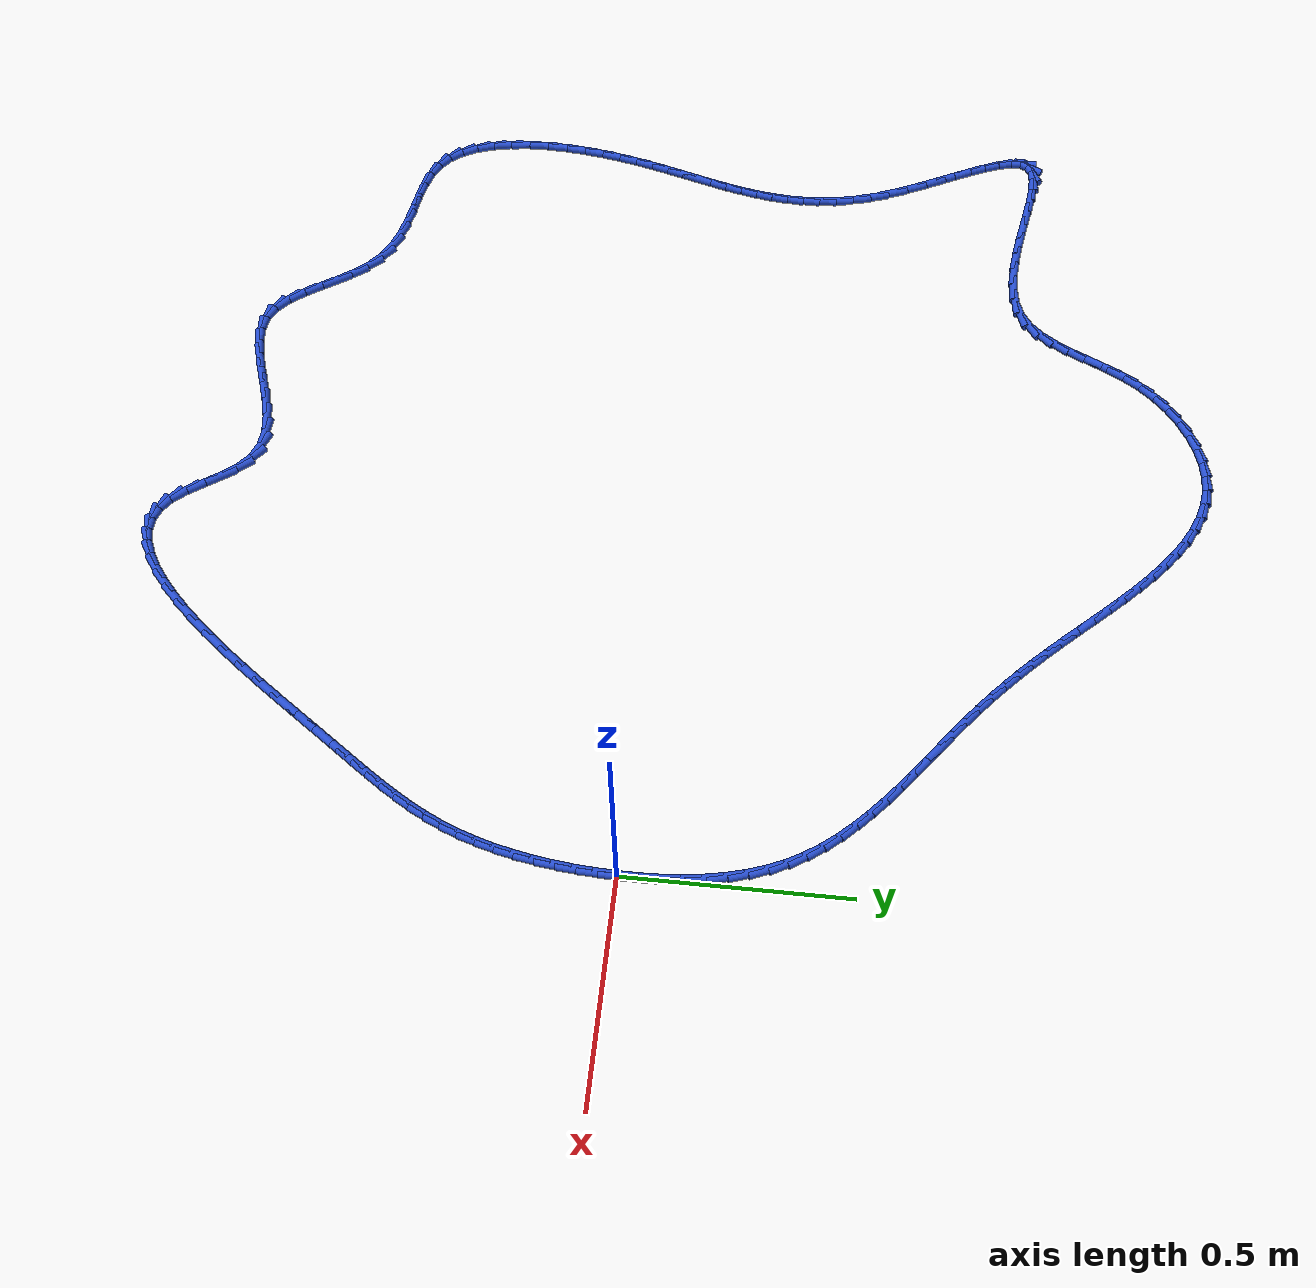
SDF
<sdf version="1.6">
 <world name="default">
  <light name="sun" type="directional">
   <pose>0 0 10 0 -0 0</pose>
   <diffuse>0.8 0.8 0.8 1</diffuse>
   <specular>0.2 0.2 0.2 1</specular>
   <attenuation>
    <range>1000</range>
    <constant>0.9</constant>
    <linear>0.01</linear>
    <quadratic>0.001</quadratic>
   </attenuation>
   <direction>-0.5 0.1 -0.9</direction>
  </light>
  <model name="ground_plane">
   <static>1</static>
   <link name="link">
    <collision name="collision">
     <geometry><plane><normal>0 0 1</normal><size>100 100</size></plane></geometry>
     <surface><friction><ode><mu>100</mu><mu2>50</mu2></ode></friction></surface>
    </collision>
    <visual name="visual">
     <cast_shadows>0</cast_shadows>
     <geometry><plane><normal>0 0 1</normal><size>100 100</size></plane></geometry>
     <material>
      <script><uri>file://media/materials/scripts/gazebo.material</uri><name>Gazebo/WhiteGlow</name></script>
     </material>
    </visual>
   </link>
  </model>
  <gravity>0 0 -9.8</gravity>
  <magnetic_field>6e-06 2.3e-05 -4.2e-05</magnetic_field>
  <atmosphere type="adiabatic"/>
  <physics name="default_physics" default="0" type="ode">
   <max_step_size>0.001</max_step_size>
   <real_time_factor>1</real_time_factor>
   <real_time_update_rate>1000</real_time_update_rate>
  </physics>
  <scene><ambient>0.4 0.4 0.4 1</ambient><background>0.7 0.7 0.7 1</background><shadows>1</shadows></scene>
  <spherical_coordinates>
   <surface_model>EARTH_WGS84</surface_model>
   <latitude_deg>0</latitude_deg>
   <longitude_deg>0</longitude_deg>
   <elevation>0</elevation>
   <heading_deg>0</heading_deg>
  </spherical_coordinates>
  <model name="line">
   <link name="link_0">
    <pose>1.734723475976807e-17 1.3877787807814457e-17 0.01 0 1.57 1.5637793598102099</pose>
    <collision name="collision">
     <geometry><cylinder><radius>0.01</radius><length>0.08</length></cylinder></geometry>
    </collision>
    <visual name="visual">
     <material>
      <script><name>Gazebo/Blue</name><uri>file://media/materials/scripts/gazebo.material</uri></script>
     </material>
     <geometry><cylinder><radius>0.01</radius><length>0.08</length></cylinder></geometry>
    </visual>
   </link>
   <link name="link_1">
    <pose>0.000321146928528067 0.04576644843174412 0.01 0 1.57 -1.538988337226999</pose>
    <collision name="collision">
     <geometry><cylinder><radius>0.01</radius><length>0.08</length></cylinder></geometry>
    </collision>
    <visual name="visual">
     <material>
      <script><name>Gazebo/Blue</name><uri>file://media/materials/scripts/gazebo.material</uri></script>
     </material>
     <geometry><cylinder><radius>0.01</radius><length>0.08</length></cylinder></geometry>
    </visual>
   </link>
   <link name="link_2">
    <pose>-0.0011294753077593519 0.09135666024666762 0.01 0 1.57 -1.4943491797490966</pose>
    <collision name="collision">
     <geometry><cylinder><radius>0.01</radius><length>0.08</length></cylinder></geometry>
    </collision>
    <visual name="visual">
     <material>
      <script><name>Gazebo/Blue</name><uri>file://media/materials/scripts/gazebo.material</uri></script>
     </material>
     <geometry><cylinder><radius>0.01</radius><length>0.08</length></cylinder></geometry>
    </visual>
   </link>
   <link name="link_3">
    <pose>-0.004588734428026658 0.1365188121148037 0.01 0 1.57 -1.4432445517743702</pose>
    <collision name="collision">
     <geometry><cylinder><radius>0.01</radius><length>0.08</length></cylinder></geometry>
    </collision>
    <visual name="visual">
     <material>
      <script><name>Gazebo/Blue</name><uri>file://media/materials/scripts/gazebo.material</uri></script>
     </material>
     <geometry><cylinder><radius>0.01</radius><length>0.08</length></cylinder></geometry>
    </visual>
   </link>
   <link name="link_4">
    <pose>-0.010293498151438294 0.1810010807061855 0.01 0 1.57 -1.3849735988600718</pose>
    <collision name="collision">
     <geometry><cylinder><radius>0.01</radius><length>0.08</length></cylinder></geometry>
    </collision>
    <visual name="visual">
     <material>
      <script><name>Gazebo/Blue</name><uri>file://media/materials/scripts/gazebo.material</uri></script>
     </material>
     <geometry><cylinder><radius>0.01</radius><length>0.08</length></cylinder></geometry>
    </visual>
   </link>
   <link name="link_5">
    <pose>-0.018480634197158667 0.22455164269084613 0.01 0 1.57 -1.3188407802872344</pose>
    <collision name="collision">
     <geometry><cylinder><radius>0.01</radius><length>0.08</length></cylinder></geometry>
    </collision>
    <visual name="visual">
     <material>
      <script><name>Gazebo/Blue</name><uri>file://media/materials/scripts/gazebo.material</uri></script>
     </material>
     <geometry><cylinder><radius>0.01</radius><length>0.08</length></cylinder></geometry>
    </visual>
   </link>
   <link name="link_6">
    <pose>-0.02938701028435222 0.2669186747388188 0.01 0 1.57 -1.2442471507943729</pose>
    <collision name="collision">
     <geometry><cylinder><radius>0.01</radius><length>0.08</length></cylinder></geometry>
    </collision>
    <visual name="visual">
     <material>
      <script><name>Gazebo/Blue</name><uri>file://media/materials/scripts/gazebo.material</uri></script>
     </material>
     <geometry><cylinder><radius>0.01</radius><length>0.08</length></cylinder></geometry>
    </visual>
   </link>
   <link name="link_7">
    <pose>-0.04324949413218336 0.3078503535201366 0.01 0 1.57 -1.1608268885653494</pose>
    <collision name="collision">
     <geometry><cylinder><radius>0.01</radius><length>0.08</length></cylinder></geometry>
    </collision>
    <visual name="visual">
     <material>
      <script><name>Gazebo/Blue</name><uri>file://media/materials/scripts/gazebo.material</uri></script>
     </material>
     <geometry><cylinder><radius>0.01</radius><length>0.08</length></cylinder></geometry>
    </visual>
   </link>
   <link name="link_8">
    <pose>-0.06030495345981654 0.3470948557048328 0.01 0 1.57 -1.0693661160491303</pose>
    <collision name="collision">
     <geometry><cylinder><radius>0.01</radius><length>0.08</length></cylinder></geometry>
    </collision>
    <visual name="visual">
     <material>
      <script><name>Gazebo/Blue</name><uri>file://media/materials/scripts/gazebo.material</uri></script>
     </material>
     <geometry><cylinder><radius>0.01</radius><length>0.08</length></cylinder></geometry>
    </visual>
   </link>
   <link name="link_9">
    <pose>-0.08076458907264737 0.38441899184581674 0.01 0 1.57 -0.9805450336766767</pose>
    <collision name="collision">
     <geometry><cylinder><radius>0.01</radius><length>0.08</length></cylinder></geometry>
    </collision>
    <visual name="visual">
     <material>
      <script><name>Gazebo/Blue</name><uri>file://media/materials/scripts/gazebo.material</uri></script>
     </material>
     <geometry><cylinder><radius>0.01</radius><length>0.08</length></cylinder></geometry>
    </visual>
   </link>
   <link name="link_10">
    <pose>-0.104494092268519 0.41984040840694775 0.01 0 1.57 -0.9025146169969304</pose>
    <collision name="collision">
     <geometry><cylinder><radius>0.01</radius><length>0.08</length></cylinder></geometry>
    </collision>
    <visual name="visual">
     <material>
      <script><name>Gazebo/Blue</name><uri>file://media/materials/scripts/gazebo.material</uri></script>
     </material>
     <geometry><cylinder><radius>0.01</radius><length>0.08</length></cylinder></geometry>
    </visual>
   </link>
   <link name="link_11">
    <pose>-0.13111161044921454 0.45355646586084775 0.01 0 1.57 -0.8357983809403094</pose>
    <collision name="collision">
     <geometry><cylinder><radius>0.01</radius><length>0.08</length></cylinder></geometry>
    </collision>
    <visual name="visual">
     <material>
      <script><name>Gazebo/Blue</name><uri>file://media/materials/scripts/gazebo.material</uri></script>
     </material>
     <geometry><cylinder><radius>0.01</radius><length>0.08</length></cylinder></geometry>
    </visual>
   </link>
   <link name="link_12">
    <pose>-0.16022990263379863 0.48576843658374286 0.01 0 1.57 -0.780205681217164</pose>
    <collision name="collision">
     <geometry><cylinder><radius>0.01</radius><length>0.08</length></cylinder></geometry>
    </collision>
    <visual name="visual">
     <material>
      <script><name>Gazebo/Blue</name><uri>file://media/materials/scripts/gazebo.material</uri></script>
     </material>
     <geometry><cylinder><radius>0.01</radius><length>0.08</length></cylinder></geometry>
    </visual>
   </link>
   <link name="link_13">
    <pose>-0.19146172784133583 0.5166775929518593 0.01 0 1.57 -0.735245622004954</pose>
    <collision name="collision">
     <geometry><cylinder><radius>0.01</radius><length>0.08</length></cylinder></geometry>
    </collision>
    <visual name="visual">
     <material>
      <script><name>Gazebo/Blue</name><uri>file://media/materials/scripts/gazebo.material</uri></script>
     </material>
     <geometry><cylinder><radius>0.01</radius><length>0.08</length></cylinder></geometry>
    </visual>
   </link>
   <link name="link_14">
    <pose>-0.2244198450908904 0.5464852073414233 0.01 0 1.57 -0.7003280463009329</pose>
    <collision name="collision">
     <geometry><cylinder><radius>0.01</radius><length>0.08</length></cylinder></geometry>
    </collision>
    <visual name="visual">
     <material>
      <script><name>Gazebo/Blue</name><uri>file://media/materials/scripts/gazebo.material</uri></script>
     </material>
     <geometry><cylinder><radius>0.01</radius><length>0.08</length></cylinder></geometry>
    </visual>
   </link>
   <link name="link_15">
    <pose>-0.2587170134015271 0.5753925521286607 0.01 0 1.57 -0.6748994606768268</pose>
    <collision name="collision">
     <geometry><cylinder><radius>0.01</radius><length>0.08</length></cylinder></geometry>
    </collision>
    <visual name="visual">
     <material>
      <script><name>Gazebo/Blue</name><uri>file://media/materials/scripts/gazebo.material</uri></script>
     </material>
     <geometry><cylinder><radius>0.01</radius><length>0.08</length></cylinder></geometry>
    </visual>
   </link>
   <link name="link_16">
    <pose>-0.2939659917923105 0.603600899689798 0.01 0 1.57 -0.6585267353213015</pose>
    <collision name="collision">
     <geometry><cylinder><radius>0.01</radius><length>0.08</length></cylinder></geometry>
    </collision>
    <visual name="visual">
     <material>
      <script><name>Gazebo/Blue</name><uri>file://media/materials/scripts/gazebo.material</uri></script>
     </material>
     <geometry><cylinder><radius>0.01</radius><length>0.08</length></cylinder></geometry>
    </visual>
   </link>
   <link name="link_17">
    <pose>-0.3297795392823049 0.631311522401061 0.01 0 1.57 -0.6509457518003419</pose>
    <collision name="collision">
     <geometry><cylinder><radius>0.01</radius><length>0.08</length></cylinder></geometry>
    </collision>
    <visual name="visual">
     <material>
      <script><name>Gazebo/Blue</name><uri>file://media/materials/scripts/gazebo.material</uri></script>
     </material>
     <geometry><cylinder><radius>0.01</radius><length>0.08</length></cylinder></geometry>
    </visual>
   </link>
   <link name="link_18">
    <pose>-0.3657704148905749 0.6587256926386761 0.01 0 1.57 -0.6520892452074681</pose>
    <collision name="collision">
     <geometry><cylinder><radius>0.01</radius><length>0.08</length></cylinder></geometry>
    </collision>
    <visual name="visual">
     <material>
      <script><name>Gazebo/Blue</name><uri>file://media/materials/scripts/gazebo.material</uri></script>
     </material>
     <geometry><cylinder><radius>0.01</radius><length>0.08</length></cylinder></geometry>
    </visual>
   </link>
   <link name="link_19">
    <pose>-0.40155137763618504 0.6860446827788694 0.01 0 1.57 -0.6621030343846273</pose>
    <collision name="collision">
     <geometry><cylinder><radius>0.01</radius><length>0.08</length></cylinder></geometry>
    </collision>
    <visual name="visual">
     <material>
      <script><name>Gazebo/Blue</name><uri>file://media/materials/scripts/gazebo.material</uri></script>
     </material>
     <geometry><cylinder><radius>0.01</radius><length>0.08</length></cylinder></geometry>
    </visual>
   </link>
   <link name="link_20">
    <pose>-0.4367351865381998 0.7134697651978669 0.01 0 1.57 -0.6812596897858104</pose>
    <collision name="collision">
     <geometry><cylinder><radius>0.01</radius><length>0.08</length></cylinder></geometry>
    </collision>
    <visual name="visual">
     <material>
      <script><name>Gazebo/Blue</name><uri>file://media/materials/scripts/gazebo.material</uri></script>
     </material>
     <geometry><cylinder><radius>0.01</radius><length>0.08</length></cylinder></geometry>
    </visual>
   </link>
   <link name="link_21">
    <pose>-0.4709403775161572 0.7412015192357346 0.01 0 1.57 -0.705810102198115</pose>
    <collision name="collision">
     <geometry><cylinder><radius>0.01</radius><length>0.08</length></cylinder></geometry>
    </collision>
    <visual name="visual">
     <material>
      <script><name>Gazebo/Blue</name><uri>file://media/materials/scripts/gazebo.material</uri></script>
     </material>
     <geometry><cylinder><radius>0.01</radius><length>0.08</length></cylinder></geometry>
    </visual>
   </link>
   <link name="link_22">
    <pose>-0.5040386381169503 0.7694101544464262 0.01 0 1.57 -0.729816989768914</pose>
    <collision name="collision">
     <geometry><cylinder><radius>0.01</radius><length>0.08</length></cylinder></geometry>
    </collision>
    <visual name="visual">
     <material>
      <script><name>Gazebo/Blue</name><uri>file://media/materials/scripts/gazebo.material</uri></script>
     </material>
     <geometry><cylinder><radius>0.01</radius><length>0.08</length></cylinder></geometry>
    </visual>
   </link>
   <link name="link_23">
    <pose>-0.5362480664177763 0.798224322627297 0.01 0 1.57 -0.7523815616115738</pose>
    <collision name="collision">
     <geometry><cylinder><radius>0.01</radius><length>0.08</length></cylinder></geometry>
    </collision>
    <visual name="visual">
     <material>
      <script><name>Gazebo/Blue</name><uri>file://media/materials/scripts/gazebo.material</uri></script>
     </material>
     <geometry><cylinder><radius>0.01</radius><length>0.08</length></cylinder></geometry>
    </visual>
   </link>
   <link name="link_24">
    <pose>-0.5678117662249231 0.8277696757188491 0.01 0 1.57 -0.7730718720368828</pose>
    <collision name="collision">
     <geometry><cylinder><radius>0.01</radius><length>0.08</length></cylinder></geometry>
    </collision>
    <visual name="visual">
     <material>
      <script><name>Gazebo/Blue</name><uri>file://media/materials/scripts/gazebo.material</uri></script>
     </material>
     <geometry><cylinder><radius>0.01</radius><length>0.08</length></cylinder></geometry>
    </visual>
   </link>
   <link name="link_25">
    <pose>-0.5989728413446782 0.8581718656615851 0.01 0 1.57 -0.7915392567322995</pose>
    <collision name="collision">
     <geometry><cylinder><radius>0.01</radius><length>0.08</length></cylinder></geometry>
    </collision>
    <visual name="visual">
     <material>
      <script><name>Gazebo/Blue</name><uri>file://media/materials/scripts/gazebo.material</uri></script>
     </material>
     <geometry><cylinder><radius>0.01</radius><length>0.08</length></cylinder></geometry>
    </visual>
   </link>
   <link name="link_26">
    <pose>-0.629974395583329 0.889556544396007 0.01 0 1.57 -0.8075355899145525</pose>
    <collision name="collision">
     <geometry><cylinder><radius>0.01</radius><length>0.08</length></cylinder></geometry>
    </collision>
    <visual name="visual">
     <material>
      <script><name>Gazebo/Blue</name><uri>file://media/materials/scripts/gazebo.material</uri></script>
     </material>
     <geometry><cylinder><radius>0.01</radius><length>0.08</length></cylinder></geometry>
    </visual>
   </link>
   <link name="link_27">
    <pose>-0.6610595327471629 0.9220493638626169 0.01 0 1.57 -0.8208083814956186</pose>
    <collision name="collision">
     <geometry><cylinder><radius>0.01</radius><length>0.08</length></cylinder></geometry>
    </collision>
    <visual name="visual">
     <material>
      <script><name>Gazebo/Blue</name><uri>file://media/materials/scripts/gazebo.material</uri></script>
     </material>
     <geometry><cylinder><radius>0.01</radius><length>0.08</length></cylinder></geometry>
    </visual>
   </link>
   <link name="link_28">
    <pose>-0.6924685098278407 0.9557653960657809 0.01 0 1.57 -0.8281107948506906</pose>
    <collision name="collision">
     <geometry><cylinder><radius>0.01</radius><length>0.08</length></cylinder></geometry>
    </collision>
    <visual name="visual">
     <material>
      <script><name>Gazebo/Blue</name><uri>file://media/materials/scripts/gazebo.material</uri></script>
     </material>
     <geometry><cylinder><radius>0.01</radius><length>0.08</length></cylinder></geometry>
    </visual>
   </link>
   <link name="link_29">
    <pose>-0.7243554612357197 0.9904996460123353 0.01 0 1.57 -0.8261800438347837</pose>
    <collision name="collision">
     <geometry><cylinder><radius>0.01</radius><length>0.08</length></cylinder></geometry>
    </collision>
    <visual name="visual">
     <material>
      <script><name>Gazebo/Blue</name><uri>file://media/materials/scripts/gazebo.material</uri></script>
     </material>
     <geometry><cylinder><radius>0.01</radius><length>0.08</length></cylinder></geometry>
    </visual>
   </link>
   <link name="link_30">
    <pose>-0.7567750779302259 1.0256775458714047 0.01 0 1.57 -0.8151564640790039</pose>
    <collision name="collision">
     <geometry><cylinder><radius>0.01</radius><length>0.08</length></cylinder></geometry>
    </collision>
    <visual name="visual">
     <material>
      <script><name>Gazebo/Blue</name><uri>file://media/materials/scripts/gazebo.material</uri></script>
     </material>
     <geometry><cylinder><radius>0.01</radius><length>0.08</length></cylinder></geometry>
    </visual>
   </link>
   <link name="link_31">
    <pose>-0.7897765225963003 1.0607039824662918 0.01 0 1.57 -0.7949311237352239</pose>
    <collision name="collision">
     <geometry><cylinder><radius>0.01</radius><length>0.08</length></cylinder></geometry>
    </collision>
    <visual name="visual">
     <material>
      <script><name>Gazebo/Blue</name><uri>file://media/materials/scripts/gazebo.material</uri></script>
     </material>
     <geometry><cylinder><radius>0.01</radius><length>0.08</length></cylinder></geometry>
    </visual>
   </link>
   <link name="link_32">
    <pose>-0.823408957918884 1.0949838426203007 0.01 0 1.57 -0.7649637945313681</pose>
    <collision name="collision">
     <geometry><cylinder><radius>0.01</radius><length>0.08</length></cylinder></geometry>
    </collision>
    <visual name="visual">
     <material>
      <script><name>Gazebo/Blue</name><uri>file://media/materials/scripts/gazebo.material</uri></script>
     </material>
     <geometry><cylinder><radius>0.01</radius><length>0.08</length></cylinder></geometry>
    </visual>
   </link>
   <link name="link_33">
    <pose>-0.8577215465829184 1.1279220131567336 0.01 0 1.57 -0.7242941805951031</pose>
    <collision name="collision">
     <geometry><cylinder><radius>0.01</radius><length>0.08</length></cylinder></geometry>
    </collision>
    <visual name="visual">
     <material>
      <script><name>Gazebo/Blue</name><uri>file://media/materials/scripts/gazebo.material</uri></script>
     </material>
     <geometry><cylinder><radius>0.01</radius><length>0.08</length></cylinder></geometry>
    </visual>
   </link>
   <link name="link_34">
    <pose>-0.8927634512733444 1.1589233808988944 0.01 0 1.57 -0.6715520813317644</pose>
    <collision name="collision">
     <geometry><cylinder><radius>0.01</radius><length>0.08</length></cylinder></geometry>
    </collision>
    <visual name="visual">
     <material>
      <script><name>Gazebo/Blue</name><uri>file://media/materials/scripts/gazebo.material</uri></script>
     </material>
     <geometry><cylinder><radius>0.01</radius><length>0.08</length></cylinder></geometry>
    </visual>
   </link>
   <link name="link_35">
    <pose>-0.928583834675103 1.1873928326700853 0.01 0 1.57 -0.6050042438337838</pose>
    <collision name="collision">
     <geometry><cylinder><radius>0.01</radius><length>0.08</length></cylinder></geometry>
    </collision>
    <visual name="visual">
     <material>
      <script><name>Gazebo/Blue</name><uri>file://media/materials/scripts/gazebo.material</uri></script>
     </material>
     <geometry><cylinder><radius>0.01</radius><length>0.08</length></cylinder></geometry>
    </visual>
   </link>
   <link name="link_36">
    <pose>-0.9652318594731354 1.2127352552936101 0.01 0 1.57 -0.5227051112629826</pose>
    <collision name="collision">
     <geometry><cylinder><radius>0.01</radius><length>0.08</length></cylinder></geometry>
    </collision>
    <visual name="visual">
     <material>
      <script><name>Gazebo/Blue</name><uri>file://media/materials/scripts/gazebo.material</uri></script>
     </material>
     <geometry><cylinder><radius>0.01</radius><length>0.08</length></cylinder></geometry>
    </visual>
   </link>
   <link name="link_37">
    <pose>-1.0027566883523829 1.2343555355927713 0.01 0 1.57 -0.4228575327056802</pose>
    <collision name="collision">
     <geometry><cylinder><radius>0.01</radius><length>0.08</length></cylinder></geometry>
    </collision>
    <visual name="visual">
     <material>
      <script><name>Gazebo/Blue</name><uri>file://media/materials/scripts/gazebo.material</uri></script>
     </material>
     <geometry><cylinder><radius>0.01</radius><length>0.08</length></cylinder></geometry>
    </visual>
   </link>
   <link name="link_38">
    <pose>-1.0412074839977856 1.2516585603908719 0.01 0 1.57 -0.30450282897941594</pose>
    <collision name="collision">
     <geometry><cylinder><radius>0.01</radius><length>0.08</length></cylinder></geometry>
    </collision>
    <visual name="visual">
     <material>
      <script><name>Gazebo/Blue</name><uri>file://media/materials/scripts/gazebo.material</uri></script>
     </material>
     <geometry><cylinder><radius>0.01</radius><length>0.08</length></cylinder></geometry>
    </visual>
   </link>
   <link name="link_39">
    <pose>-1.0806334090942862 1.2640492165112158 0.01 0 1.57 -0.1685496304630655</pose>
    <collision name="collision">
     <geometry><cylinder><radius>0.01</radius><length>0.08</length></cylinder></geometry>
    </collision>
    <visual name="visual">
     <material>
      <script><name>Gazebo/Blue</name><uri>file://media/materials/scripts/gazebo.material</uri></script>
     </material>
     <geometry><cylinder><radius>0.01</radius><length>0.08</length></cylinder></geometry>
    </visual>
   </link>
   <link name="link_40">
    <pose>-1.1210836263268247 1.2709323907771055 0.01 0 1.57 -0.018964667046183915</pose>
    <collision name="collision">
     <geometry><cylinder><radius>0.01</radius><length>0.08</length></cylinder></geometry>
    </collision>
    <visual name="visual">
     <material>
      <script><name>Gazebo/Blue</name><uri>file://media/materials/scripts/gazebo.material</uri></script>
     </material>
     <geometry><cylinder><radius>0.01</radius><length>0.08</length></cylinder></geometry>
    </visual>
   </link>
   <link name="link_41">
    <pose>-1.1626014998685155 1.271719857833985 0.01 0 1.57 0.12982514322320207</pose>
    <collision name="collision">
     <geometry><cylinder><radius>0.01</radius><length>0.08</length></cylinder></geometry>
    </collision>
    <visual name="visual">
     <material>
      <script><name>Gazebo/Blue</name><uri>file://media/materials/scripts/gazebo.material</uri></script>
     </material>
     <geometry><cylinder><radius>0.01</radius><length>0.08</length></cylinder></geometry>
    </visual>
   </link>
   <link name="link_42">
    <pose>-1.2049174655375265 1.2661951075045736 0.01 0 1.57 0.2649828141941581</pose>
    <collision name="collision">
     <geometry><cylinder><radius>0.01</radius><length>0.08</length></cylinder></geometry>
    </collision>
    <visual name="visual">
     <material>
      <script><name>Gazebo/Blue</name><uri>file://media/materials/scripts/gazebo.material</uri></script>
     </material>
     <geometry><cylinder><radius>0.01</radius><length>0.08</length></cylinder></geometry>
    </visual>
   </link>
   <link name="link_43">
    <pose>-1.2472960321741364 1.2546950857827777 0.01 0 1.57 0.38929277703181014</pose>
    <collision name="collision">
     <geometry><cylinder><radius>0.01</radius><length>0.08</length></cylinder></geometry>
    </collision>
    <visual name="visual">
     <material>
      <script><name>Gazebo/Blue</name><uri>file://media/materials/scripts/gazebo.material</uri></script>
     </material>
     <geometry><cylinder><radius>0.01</radius><length>0.08</length></cylinder></geometry>
    </visual>
   </link>
   <link name="link_44">
    <pose>-1.288963782295939 1.2376017898364782 0.01 0 1.57 0.5067256533940862</pose>
    <collision name="collision">
     <geometry><cylinder><radius>0.01</radius><length>0.08</length></cylinder></geometry>
    </collision>
    <visual name="visual">
     <material>
      <script><name>Gazebo/Blue</name><uri>file://media/materials/scripts/gazebo.material</uri></script>
     </material>
     <geometry><cylinder><radius>0.01</radius><length>0.08</length></cylinder></geometry>
    </visual>
   </link>
   <link name="link_45">
    <pose>-1.3291472984205273 1.2152972168335543 0.01 0 1.57 0.6210163978946417</pose>
    <collision name="collision">
     <geometry><cylinder><radius>0.01</radius><length>0.08</length></cylinder></geometry>
    </collision>
    <visual name="visual">
     <material>
      <script><name>Gazebo/Blue</name><uri>file://media/materials/scripts/gazebo.material</uri></script>
     </material>
     <geometry><cylinder><radius>0.01</radius><length>0.08</length></cylinder></geometry>
    </visual>
   </link>
   <link name="link_46">
    <pose>-1.367073163065494 1.1881633639418878 0.01 0 1.57 0.7355918722484676</pose>
    <collision name="collision">
     <geometry><cylinder><radius>0.01</radius><length>0.08</length></cylinder></geometry>
    </collision>
    <visual name="visual">
     <material>
      <script><name>Gazebo/Blue</name><uri>file://media/materials/scripts/gazebo.material</uri></script>
     </material>
     <geometry><cylinder><radius>0.01</radius><length>0.08</length></cylinder></geometry>
    </visual>
   </link>
   <link name="link_47">
    <pose>-1.4019679587484346 1.156582228329358 0.01 0 1.57 0.8535623254408317</pose>
    <collision name="collision">
     <geometry><cylinder><radius>0.01</radius><length>0.08</length></cylinder></geometry>
    </collision>
    <visual name="visual">
     <material>
      <script><name>Gazebo/Blue</name><uri>file://media/materials/scripts/gazebo.material</uri></script>
     </material>
     <geometry><cylinder><radius>0.01</radius><length>0.08</length></cylinder></geometry>
    </visual>
   </link>
   <link name="link_48">
    <pose>-1.4330582679869406 1.1209358071638464 0.01 0 1.57 0.9724983486565782</pose>
    <collision name="collision">
     <geometry><cylinder><radius>0.01</radius><length>0.08</length></cylinder></geometry>
    </collision>
    <visual name="visual">
     <material>
      <script><name>Gazebo/Blue</name><uri>file://media/materials/scripts/gazebo.material</uri></script>
     </material>
     <geometry><cylinder><radius>0.01</radius><length>0.08</length></cylinder></geometry>
    </visual>
   </link>
   <link name="link_49">
    <pose>-1.4597882550750798 1.0817216396972555 0.01 0 1.57 1.0597664233551962</pose>
    <collision name="collision">
     <geometry><cylinder><radius>0.01</radius><length>0.08</length></cylinder></geometry>
    </collision>
    <visual name="visual">
     <material>
      <script><name>Gazebo/Blue</name><uri>file://media/materials/scripts/gazebo.material</uri></script>
     </material>
     <geometry><cylinder><radius>0.01</radius><length>0.08</length></cylinder></geometry>
    </visual>
   </link>
   <link name="link_50">
    <pose>-1.4830626939414202 1.0402128902538126 0.01 0 1.57 1.1030015402741207</pose>
    <collision name="collision">
     <geometry><cylinder><radius>0.01</radius><length>0.08</length></cylinder></geometry>
    </collision>
    <visual name="visual">
     <material>
      <script><name>Gazebo/Blue</name><uri>file://media/materials/scripts/gazebo.material</uri></script>
     </material>
     <geometry><cylinder><radius>0.01</radius><length>0.08</length></cylinder></geometry>
    </visual>
   </link>
   <link name="link_51">
    <pose>-1.5043874544323719 0.99800192210984 0.01 0 1.57 1.1028425541408635</pose>
    <collision name="collision">
     <geometry><cylinder><radius>0.01</radius><length>0.08</length></cylinder></geometry>
    </collision>
    <visual name="visual">
     <material>
      <script><name>Gazebo/Blue</name><uri>file://media/materials/scripts/gazebo.material</uri></script>
     </material>
     <geometry><cylinder><radius>0.01</radius><length>0.08</length></cylinder></geometry>
    </visual>
   </link>
   <link name="link_52">
    <pose>-1.5252702661744886 0.9566820861375726 0.01 0 1.57 1.0563806151073565</pose>
    <collision name="collision">
     <geometry><cylinder><radius>0.01</radius><length>0.08</length></cylinder></geometry>
    </collision>
    <visual name="visual">
     <material>
      <script><name>Gazebo/Blue</name><uri>file://media/materials/scripts/gazebo.material</uri></script>
     </material>
     <geometry><cylinder><radius>0.01</radius><length>0.08</length></cylinder></geometry>
    </visual>
   </link>
   <link name="link_53">
    <pose>-1.5472188587943236 0.9178467332092475 0.01 0 1.57 0.9563756803726114</pose>
    <collision name="collision">
     <geometry><cylinder><radius>0.01</radius><length>0.08</length></cylinder></geometry>
    </collision>
    <visual name="visual">
     <material>
      <script><name>Gazebo/Blue</name><uri>file://media/materials/scripts/gazebo.material</uri></script>
     </material>
     <geometry><cylinder><radius>0.01</radius><length>0.08</length></cylinder></geometry>
    </visual>
   </link>
   <link name="link_54">
    <pose>-1.571740961918429 0.8830892141970994 0.01 0 1.57 0.7937701929431378</pose>
    <collision name="collision">
     <geometry><cylinder><radius>0.01</radius><length>0.08</length></cylinder></geometry>
    </collision>
    <visual name="visual">
     <material>
      <script><name>Gazebo/Blue</name><uri>file://media/materials/scripts/gazebo.material</uri></script>
     </material>
     <geometry><cylinder><radius>0.01</radius><length>0.08</length></cylinder></geometry>
    </visual>
   </link>
   <link name="link_55">
    <pose>-1.6003443051733588 0.8540028799733638 0.01 0 1.57 0.5680406840270082</pose>
    <collision name="collision">
     <geometry><cylinder><radius>0.01</radius><length>0.08</length></cylinder></geometry>
    </collision>
    <visual name="visual">
     <material>
      <script><name>Gazebo/Blue</name><uri>file://media/materials/scripts/gazebo.material</uri></script>
     </material>
     <geometry><cylinder><radius>0.01</radius><length>0.08</length></cylinder></geometry>
    </visual>
   </link>
   <link name="link_56">
    <pose>-1.6345366181856658 0.8321810814102775 0.01 0 1.57 0.31708209583452684</pose>
    <collision name="collision">
     <geometry><cylinder><radius>0.01</radius><length>0.08</length></cylinder></geometry>
    </collision>
    <visual name="visual">
     <material>
      <script><name>Gazebo/Blue</name><uri>file://media/materials/scripts/gazebo.material</uri></script>
     </material>
     <geometry><cylinder><radius>0.01</radius><length>0.08</length></cylinder></geometry>
    </visual>
   </link>
   <link name="link_57">
    <pose>-1.6753869330593354 0.8187758798676216 0.01 0 1.57 0.1252555673458638</pose>
    <collision name="collision">
     <geometry><cylinder><radius>0.01</radius><length>0.08</length></cylinder></geometry>
    </collision>
    <visual name="visual">
     <material>
      <script><name>Gazebo/Blue</name><uri>file://media/materials/scripts/gazebo.material</uri></script>
     </material>
     <geometry><cylinder><radius>0.01</radius><length>0.08</length></cylinder></geometry>
    </visual>
   </link>
   <link name="link_58">
    <pose>-1.7219497785698106 0.8129129309336403 0.01 0 1.57 -0.004406884729331305</pose>
    <collision name="collision">
     <geometry><cylinder><radius>0.01</radius><length>0.08</length></cylinder></geometry>
    </collision>
    <visual name="visual">
     <material>
      <script><name>Gazebo/Blue</name><uri>file://media/materials/scripts/gazebo.material</uri></script>
     </material>
     <geometry><cylinder><radius>0.01</radius><length>0.08</length></cylinder></geometry>
    </visual>
   </link>
   <link name="link_59">
    <pose>-1.7727017983411066 0.8131365906824263 0.01 0 1.57 -0.09063041390418657</pose>
    <collision name="collision">
     <geometry><cylinder><radius>0.01</radius><length>0.08</length></cylinder></geometry>
    </collision>
    <visual name="visual">
     <material>
      <script><name>Gazebo/Blue</name><uri>file://media/materials/scripts/gazebo.material</uri></script>
     </material>
     <geometry><cylinder><radius>0.01</radius><length>0.08</length></cylinder></geometry>
    </visual>
   </link>
   <link name="link_60">
    <pose>-1.8261195869790288 0.8179911658802441 0.01 0 1.57 -0.14612430506655147</pose>
    <collision name="collision">
     <geometry><cylinder><radius>0.01</radius><length>0.08</length></cylinder></geometry>
    </collision>
    <visual name="visual">
     <material>
      <script><name>Gazebo/Blue</name><uri>file://media/materials/scripts/gazebo.material</uri></script>
     </material>
     <geometry><cylinder><radius>0.01</radius><length>0.08</length></cylinder></geometry>
    </visual>
   </link>
   <link name="link_61">
    <pose>-1.8806797390893828 0.8260209632933585 0.01 0 1.57 -0.1780408511313158</pose>
    <collision name="collision">
     <geometry><cylinder><radius>0.01</radius><length>0.08</length></cylinder></geometry>
    </collision>
    <visual name="visual">
     <material>
      <script><name>Gazebo/Blue</name><uri>file://media/materials/scripts/gazebo.material</uri></script>
     </material>
     <geometry><cylinder><radius>0.01</radius><length>0.08</length></cylinder></geometry>
    </visual>
   </link>
   <link name="link_62">
    <pose>-1.9348588492779732 0.8357702896880335 0.01 0 1.57 -0.1892566009196271</pose>
    <collision name="collision">
     <geometry><cylinder><radius>0.01</radius><length>0.08</length></cylinder></geometry>
    </collision>
    <visual name="visual">
     <material>
      <script><name>Gazebo/Blue</name><uri>file://media/materials/scripts/gazebo.material</uri></script>
     </material>
     <geometry><cylinder><radius>0.01</radius><length>0.08</length></cylinder></geometry>
    </visual>
   </link>
   <link name="link_63">
    <pose>-1.9871335121506055 0.8457834518305339 0.01 0 1.57 -0.17866553716962968</pose>
    <collision name="collision">
     <geometry><cylinder><radius>0.01</radius><length>0.08</length></cylinder></geometry>
    </collision>
    <visual name="visual">
     <material>
      <script><name>Gazebo/Blue</name><uri>file://media/materials/scripts/gazebo.material</uri></script>
     </material>
     <geometry><cylinder><radius>0.01</radius><length>0.08</length></cylinder></geometry>
    </visual>
   </link>
   <link name="link_64">
    <pose>-2.0359803223130837 0.8546047564871238 0.01 0 1.57 -0.1397299165177419</pose>
    <collision name="collision">
     <geometry><cylinder><radius>0.01</radius><length>0.08</length></cylinder></geometry>
    </collision>
    <visual name="visual">
     <material>
      <script><name>Gazebo/Blue</name><uri>file://media/materials/scripts/gazebo.material</uri></script>
     </material>
     <geometry><cylinder><radius>0.01</radius><length>0.08</length></cylinder></geometry>
    </visual>
   </link>
   <link name="link_65">
    <pose>-2.079875874371214 0.8607785104240677 0.01 0 1.57 -0.055273966449175906</pose>
    <collision name="collision">
     <geometry><cylinder><radius>0.01</radius><length>0.08</length></cylinder></geometry>
    </collision>
    <visual name="visual">
     <material>
      <script><name>Gazebo/Blue</name><uri>file://media/materials/scripts/gazebo.material</uri></script>
     </material>
     <geometry><cylinder><radius>0.01</radius><length>0.08</length></cylinder></geometry>
    </visual>
   </link>
   <link name="link_66">
    <pose>-2.1172967629308026 0.8628490204076306 0.01 0 1.57 0.11801106076208959</pose>
    <collision name="collision">
     <geometry><cylinder><radius>0.01</radius><length>0.08</length></cylinder></geometry>
    </collision>
    <visual name="visual">
     <material>
      <script><name>Gazebo/Blue</name><uri>file://media/materials/scripts/gazebo.material</uri></script>
     </material>
     <geometry><cylinder><radius>0.01</radius><length>0.08</length></cylinder></geometry>
    </visual>
   </link>
   <link name="link_67">
    <pose>-2.1467195825976524 0.8593605932040761 0.01 0 1.57 0.48560518540509556</pose>
    <collision name="collision">
     <geometry><cylinder><radius>0.01</radius><length>0.08</length></cylinder></geometry>
    </collision>
    <visual name="visual">
     <material>
      <script><name>Gazebo/Blue</name><uri>file://media/materials/scripts/gazebo.material</uri></script>
     </material>
     <geometry><cylinder><radius>0.01</radius><length>0.08</length></cylinder></geometry>
    </visual>
   </link>
   <link name="link_68">
    <pose>-2.1666209279775708 0.8488575355796691 0.01 0 1.57 1.1172285961468695</pose>
    <collision name="collision">
     <geometry><cylinder><radius>0.01</radius><length>0.08</length></cylinder></geometry>
    </collision>
    <visual name="visual">
     <material>
      <script><name>Gazebo/Blue</name><uri>file://media/materials/scripts/gazebo.material</uri></script>
     </material>
     <geometry><cylinder><radius>0.01</radius><length>0.08</length></cylinder></geometry>
    </visual>
   </link>
   <link name="link_69">
    <pose>-2.175760031778402 0.830109229717225 0.01 0 1.57 -1.5399905865385248</pose>
    <collision name="collision">
     <geometry><cylinder><radius>0.01</radius><length>0.08</length></cylinder></geometry>
    </collision>
    <visual name="visual">
     <material>
      <script><name>Gazebo/Blue</name><uri>file://media/materials/scripts/gazebo.material</uri></script>
     </material>
     <geometry><cylinder><radius>0.01</radius><length>0.08</length></cylinder></geometry>
    </visual>
   </link>
   <link name="link_70">
    <pose>-2.1749404570514757 0.803513035415826 0.01 0 1.57 -1.3049530049283278</pose>
    <collision name="collision">
     <geometry><cylinder><radius>0.01</radius><length>0.08</length></cylinder></geometry>
    </collision>
    <visual name="visual">
     <material>
      <script><name>Gazebo/Blue</name><uri>file://media/materials/scripts/gazebo.material</uri></script>
     </material>
     <geometry><cylinder><radius>0.01</radius><length>0.08</length></cylinder></geometry>
    </visual>
   </link>
   <link name="link_71">
    <pose>-2.1658648980468342 0.7701823246739803 0.01 0 1.57 -1.1892842040003102</pose>
    <collision name="collision">
     <geometry><cylinder><radius>0.01</radius><length>0.08</length></cylinder></geometry>
    </collision>
    <visual name="visual">
     <material>
      <script><name>Gazebo/Blue</name><uri>file://media/materials/scripts/gazebo.material</uri></script>
     </material>
     <geometry><cylinder><radius>0.01</radius><length>0.08</length></cylinder></geometry>
    </visual>
   </link>
   <link name="link_72">
    <pose>-2.1502399354960393 0.7312335644425086 0.01 0 1.57 -1.1305663218115263</pose>
    <collision name="collision">
     <geometry><cylinder><radius>0.01</radius><length>0.08</length></cylinder></geometry>
    </collision>
    <visual name="visual">
     <material>
      <script><name>Gazebo/Blue</name><uri>file://media/materials/scripts/gazebo.material</uri></script>
     </material>
     <geometry><cylinder><radius>0.01</radius><length>0.08</length></cylinder></geometry>
    </visual>
   </link>
   <link name="link_73">
    <pose>-2.129772150130653 0.6877832216722303 0.01 0 1.57 -1.1039716087572669</pose>
    <collision name="collision">
     <geometry><cylinder><radius>0.01</radius><length>0.08</length></cylinder></geometry>
    </collision>
    <visual name="visual">
     <material>
      <script><name>Gazebo/Blue</name><uri>file://media/materials/scripts/gazebo.material</uri></script>
     </material>
     <geometry><cylinder><radius>0.01</radius><length>0.08</length></cylinder></geometry>
    </visual>
   </link>
   <link name="link_74">
    <pose>-2.106168122682237 0.640947763313965 0.01 0 1.57 -1.099332780459465</pose>
    <collision name="collision">
     <geometry><cylinder><radius>0.01</radius><length>0.08</length></cylinder></geometry>
    </collision>
    <visual name="visual">
     <material>
      <script><name>Gazebo/Blue</name><uri>file://media/materials/scripts/gazebo.material</uri></script>
     </material>
     <geometry><cylinder><radius>0.01</radius><length>0.08</length></cylinder></geometry>
    </visual>
   </link>
   <link name="link_75">
    <pose>-2.0811344338823554 0.5918436563185336 0.01 0 1.57 -1.1130778709149476</pose>
    <collision name="collision">
     <geometry><cylinder><radius>0.01</radius><length>0.08</length></cylinder></geometry>
    </collision>
    <visual name="visual">
     <material>
      <script><name>Gazebo/Blue</name><uri>file://media/materials/scripts/gazebo.material</uri></script>
     </material>
     <geometry><cylinder><radius>0.01</radius><length>0.08</length></cylinder></geometry>
    </visual>
   </link>
   <link name="link_76">
    <pose>-2.056377664462568 0.5415873676367554 0.01 0 1.57 -1.1455990314817999</pose>
    <collision name="collision">
     <geometry><cylinder><radius>0.01</radius><length>0.08</length></cylinder></geometry>
    </collision>
    <visual name="visual">
     <material>
      <script><name>Gazebo/Blue</name><uri>file://media/materials/scripts/gazebo.material</uri></script>
     </material>
     <geometry><cylinder><radius>0.01</radius><length>0.08</length></cylinder></geometry>
    </visual>
   </link>
   <link name="link_77">
    <pose>-2.033604395154438 0.4912953642194497 0.01 0 1.57 -1.2007852691958396</pose>
    <collision name="collision">
     <geometry><cylinder><radius>0.01</radius><length>0.08</length></cylinder></geometry>
    </collision>
    <visual name="visual">
     <material>
      <script><name>Gazebo/Blue</name><uri>file://media/materials/scripts/gazebo.material</uri></script>
     </material>
     <geometry><cylinder><radius>0.01</radius><length>0.08</length></cylinder></geometry>
    </visual>
   </link>
   <link name="link_78">
    <pose>-2.0145149988058737 0.4420801456520575 0.01 0 1.57 -1.276530668402631</pose>
    <collision name="collision">
     <geometry><cylinder><radius>0.01</radius><length>0.08</length></cylinder></geometry>
    </collision>
    <visual name="visual">
     <material>
      <script><name>Gazebo/Blue</name><uri>file://media/materials/scripts/gazebo.material</uri></script>
     </material>
     <geometry><cylinder><radius>0.01</radius><length>0.08</length></cylinder></geometry>
    </visual>
   </link>
   <link name="link_79">
    <pose>-2.00013179042895 0.39462087492201875 0.01 0 1.57 -1.3573937975804207</pose>
    <collision name="collision">
     <geometry><cylinder><radius>0.01</radius><length>0.08</length></cylinder></geometry>
    </collision>
    <visual name="visual">
     <material>
      <script><name>Gazebo/Blue</name><uri>file://media/materials/scripts/gazebo.material</uri></script>
     </material>
     <geometry><cylinder><radius>0.01</radius><length>0.08</length></cylinder></geometry>
    </visual>
   </link>
   <link name="link_80">
    <pose>-1.9901977870320173 0.3487791348407695 0.01 0 1.57 -1.4392053865078431</pose>
    <collision name="collision">
     <geometry><cylinder><radius>0.01</radius><length>0.08</length></cylinder></geometry>
    </collision>
    <visual name="visual">
     <material>
      <script><name>Gazebo/Blue</name><uri>file://media/materials/scripts/gazebo.material</uri></script>
     </material>
     <geometry><cylinder><radius>0.01</radius><length>0.08</length></cylinder></geometry>
    </visual>
   </link>
   <link name="link_81">
    <pose>-1.984314136341671 0.30432584168856236 0.01 0 1.57 -1.519283896503375</pose>
    <collision name="collision">
     <geometry><cylinder><radius>0.01</radius><length>0.08</length></cylinder></geometry>
    </collision>
    <visual name="visual">
     <material>
      <script><name>Gazebo/Blue</name><uri>file://media/materials/scripts/gazebo.material</uri></script>
     </material>
     <geometry><cylinder><radius>0.01</radius><length>0.08</length></cylinder></geometry>
    </visual>
   </link>
   <link name="link_82">
    <pose>-1.9820819860845071 0.2610319117456503 0.01 0 1.57 1.546711986353489</pose>
    <collision name="collision">
     <geometry><cylinder><radius>0.01</radius><length>0.08</length></cylinder></geometry>
    </collision>
    <visual name="visual">
     <material>
      <script><name>Gazebo/Blue</name><uri>file://media/materials/scripts/gazebo.material</uri></script>
     </material>
     <geometry><cylinder><radius>0.01</radius><length>0.08</length></cylinder></geometry>
    </visual>
   </link>
   <link name="link_83">
    <pose>-1.9831024839871223 0.2186682612922875 0.01 0 1.57 1.4780705469140105</pose>
    <collision name="collision">
     <geometry><cylinder><radius>0.01</radius><length>0.08</length></cylinder></geometry>
    </collision>
    <visual name="visual">
     <material>
      <script><name>Gazebo/Blue</name><uri>file://media/materials/scripts/gazebo.material</uri></script>
     </material>
     <geometry><cylinder><radius>0.01</radius><length>0.08</length></cylinder></geometry>
    </visual>
   </link>
   <link name="link_84">
    <pose>-1.9869767777761118 0.17700580660872647 0.01 0 1.57 1.4183305287716659</pose>
    <collision name="collision">
     <geometry><cylinder><radius>0.01</radius><length>0.08</length></cylinder></geometry>
    </collision>
    <visual name="visual">
     <material>
      <script><name>Gazebo/Blue</name><uri>file://media/materials/scripts/gazebo.material</uri></script>
     </material>
     <geometry><cylinder><radius>0.01</radius><length>0.08</length></cylinder></geometry>
    </visual>
   </link>
   <link name="link_85">
    <pose>-1.9933060151780726 0.13581546397522112 0.01 0 1.57 1.3688056384747098</pose>
    <collision name="collision">
     <geometry><cylinder><radius>0.01</radius><length>0.08</length></cylinder></geometry>
    </collision>
    <visual name="visual">
     <material>
      <script><name>Gazebo/Blue</name><uri>file://media/materials/scripts/gazebo.material</uri></script>
     </material>
     <geometry><cylinder><radius>0.01</radius><length>0.08</length></cylinder></geometry>
    </visual>
   </link>
   <link name="link_86">
    <pose>-2.0016913439196005 0.09486814967202445 0.01 0 1.57 1.3302089107468724</pose>
    <collision name="collision">
     <geometry><cylinder><radius>0.01</radius><length>0.08</length></cylinder></geometry>
    </collision>
    <visual name="visual">
     <material>
      <script><name>Gazebo/Blue</name><uri>file://media/materials/scripts/gazebo.material</uri></script>
     </material>
     <geometry><cylinder><radius>0.01</radius><length>0.08</length></cylinder></geometry>
    </visual>
   </link>
   <link name="link_87">
    <pose>-2.0117339117272914 0.05393477997938975 0.01 0 1.57 1.3027664596216624</pose>
    <collision name="collision">
     <geometry><cylinder><radius>0.01</radius><length>0.08</length></cylinder></geometry>
    </collision>
    <visual name="visual">
     <material>
      <script><name>Gazebo/Blue</name><uri>file://media/materials/scripts/gazebo.material</uri></script>
     </material>
     <geometry><cylinder><radius>0.01</radius><length>0.08</length></cylinder></geometry>
    </visual>
   </link>
   <link name="link_88">
    <pose>-2.0230348663277415 0.01278627117757035 0.01 0 1.57 1.28635365708335</pose>
    <collision name="collision">
     <geometry><cylinder><radius>0.01</radius><length>0.08</length></cylinder></geometry>
    </collision>
    <visual name="visual">
     <material>
      <script><name>Gazebo/Blue</name><uri>file://media/materials/scripts/gazebo.material</uri></script>
     </material>
     <geometry><cylinder><radius>0.01</radius><length>0.08</length></cylinder></geometry>
    </visual>
   </link>
   <link name="link_89">
    <pose>-2.0351953554475473 -0.028806460453181387 0.01 0 1.57 1.2806128659464728</pose>
    <collision name="collision">
     <geometry><cylinder><radius>0.01</radius><length>0.08</length></cylinder></geometry>
    </collision>
    <visual name="visual">
     <material>
      <script><name>Gazebo/Blue</name><uri>file://media/materials/scripts/gazebo.material</uri></script>
     </material>
     <geometry><cylinder><radius>0.01</radius><length>0.08</length></cylinder></geometry>
    </visual>
   </link>
   <link name="link_90">
    <pose>-2.0478165268133033 -0.07107249863261045 0.01 0 1.57 1.285034770660092</pose>
    <collision name="collision">
     <geometry><cylinder><radius>0.01</radius><length>0.08</length></cylinder></geometry>
    </collision>
    <visual name="visual">
     <material>
      <script><name>Gazebo/Blue</name><uri>file://media/materials/scripts/gazebo.material</uri></script>
     </material>
     <geometry><cylinder><radius>0.01</radius><length>0.08</length></cylinder></geometry>
    </visual>
   </link>
   <link name="link_91">
    <pose>-2.0604995281516083 -0.11424092708046442 0.01 0 1.57 1.2990019773623045</pose>
    <collision name="collision">
     <geometry><cylinder><radius>0.01</radius><length>0.08</length></cylinder></geometry>
    </collision>
    <visual name="visual">
     <material>
      <script><name>Gazebo/Blue</name><uri>file://media/materials/scripts/gazebo.material</uri></script>
     </material>
     <geometry><cylinder><radius>0.01</radius><length>0.08</length></cylinder></geometry>
    </visual>
   </link>
   <link name="link_92">
    <pose>-2.072845507189056 -0.15854082951648998 0.01 0 1.57 1.3218024991492292</pose>
    <collision name="collision">
     <geometry><cylinder><radius>0.01</radius><length>0.08</length></cylinder></geometry>
    </collision>
    <visual name="visual">
     <material>
      <script><name>Gazebo/Blue</name><uri>file://media/materials/scripts/gazebo.material</uri></script>
     </material>
     <geometry><cylinder><radius>0.01</radius><length>0.08</length></cylinder></geometry>
    </visual>
   </link>
   <link name="link_93">
    <pose>-2.084455611652244 -0.2042012896604338 0.01 0 1.57 1.3526244758456478</pose>
    <collision name="collision">
     <geometry><cylinder><radius>0.01</radius><length>0.08</length></cylinder></geometry>
    </collision>
    <visual name="visual">
     <material>
      <script><name>Gazebo/Blue</name><uri>file://media/materials/scripts/gazebo.material</uri></script>
     </material>
     <geometry><cylinder><radius>0.01</radius><length>0.08</length></cylinder></geometry>
    </visual>
   </link>
   <link name="link_94">
    <pose>-2.094930989267768 -0.2514513912320436 0.01 0 1.57 1.390514569202517</pose>
    <collision name="collision">
     <geometry><cylinder><radius>0.01</radius><length>0.08</length></cylinder></geometry>
    </collision>
    <visual name="visual">
     <material>
      <script><name>Gazebo/Blue</name><uri>file://media/materials/scripts/gazebo.material</uri></script>
     </material>
     <geometry><cylinder><radius>0.01</radius><length>0.08</length></cylinder></geometry>
    </visual>
   </link>
   <link name="link_95">
    <pose>-2.1038724273375697 -0.30050991803590477 0.01 0 1.57 1.4335396641100588</pose>
    <collision name="collision">
     <geometry><cylinder><radius>0.01</radius><length>0.08</length></cylinder></geometry>
    </collision>
    <visual name="visual">
     <material>
      <script><name>Gazebo/Blue</name><uri>file://media/materials/scripts/gazebo.material</uri></script>
     </material>
     <geometry><cylinder><radius>0.01</radius><length>0.08</length></cylinder></geometry>
    </visual>
   </link>
   <link name="link_96">
    <pose>-2.1108644472879527 -0.35113082124837613 0.01 0 1.57 1.4812664202128558</pose>
    <collision name="collision">
     <geometry><cylinder><radius>0.01</radius><length>0.08</length></cylinder></geometry>
    </collision>
    <visual name="visual">
     <material>
      <script><name>Gazebo/Blue</name><uri>file://media/materials/scripts/gazebo.material</uri></script>
     </material>
     <geometry><cylinder><radius>0.01</radius><length>0.08</length></cylinder></geometry>
    </visual>
   </link>
   <link name="link_97">
    <pose>-2.1154690351926986 -0.40242405553601623 0.01 0 1.57 1.5359769980371614</pose>
    <collision name="collision">
     <geometry><cylinder><radius>0.01</radius><length>0.08</length></cylinder></geometry>
    </collision>
    <visual name="visual">
     <material>
      <script><name>Gazebo/Blue</name><uri>file://media/materials/scripts/gazebo.material</uri></script>
     </material>
     <geometry><cylinder><radius>0.01</radius><length>0.08</length></cylinder></geometry>
    </visual>
   </link>
   <link name="link_98">
    <pose>-2.117246520878277 -0.45345224471101825 0.01 0 1.57 -1.5409153335677868</pose>
    <collision name="collision">
     <geometry><cylinder><radius>0.01</radius><length>0.08</length></cylinder></geometry>
    </collision>
    <visual name="visual">
     <material>
      <script><name>Gazebo/Blue</name><uri>file://media/materials/scripts/gazebo.material</uri></script>
     </material>
     <geometry><cylinder><radius>0.01</radius><length>0.08</length></cylinder></geometry>
    </visual>
   </link>
   <link name="link_99">
    <pose>-2.1157572341711566 -0.5032780125855766 0.01 0 1.57 -1.4622672605901679</pose>
    <collision name="collision">
     <geometry><cylinder><radius>0.01</radius><length>0.08</length></cylinder></geometry>
    </collision>
    <visual name="visual">
     <material>
      <script><name>Gazebo/Blue</name><uri>file://media/materials/scripts/gazebo.material</uri></script>
     </material>
     <geometry><cylinder><radius>0.01</radius><length>0.08</length></cylinder></geometry>
    </visual>
   </link>
   <link name="link_100">
    <pose>-2.1105615048978077 -0.5509639829718826 0.01 0 1.57 -1.3643625385766562</pose>
    <collision name="collision">
     <geometry><cylinder><radius>0.01</radius><length>0.08</length></cylinder></geometry>
    </collision>
    <visual name="visual">
     <material>
      <script><name>Gazebo/Blue</name><uri>file://media/materials/scripts/gazebo.material</uri></script>
     </material>
     <geometry><cylinder><radius>0.01</radius><length>0.08</length></cylinder></geometry>
    </visual>
   </link>
   <link name="link_101">
    <pose>-2.1012196628847004 -0.5955727796821312 0.01 0 1.57 -1.24028743226745</pose>
    <collision name="collision">
     <geometry><cylinder><radius>0.01</radius><length>0.08</length></cylinder></geometry>
    </collision>
    <visual name="visual">
     <material>
      <script><name>Gazebo/Blue</name><uri>file://media/materials/scripts/gazebo.material</uri></script>
     </material>
     <geometry><cylinder><radius>0.01</radius><length>0.08</length></cylinder></geometry>
    </visual>
   </link>
   <link name="link_102">
    <pose>-2.087292037958303 -0.6361670265285148 0.01 0 1.57 -1.082066518433263</pose>
    <collision name="collision">
     <geometry><cylinder><radius>0.01</radius><length>0.08</length></cylinder></geometry>
    </collision>
    <visual name="visual">
     <material>
      <script><name>Gazebo/Blue</name><uri>file://media/materials/scripts/gazebo.material</uri></script>
     </material>
     <geometry><cylinder><radius>0.01</radius><length>0.08</length></cylinder></geometry>
    </visual>
   </link>
   <link name="link_103">
    <pose>-2.068338959945086 -0.6718093473232277 0.01 0 1.57 -0.8835622900111554</pose>
    <collision name="collision">
     <geometry><cylinder><radius>0.01</radius><length>0.08</length></cylinder></geometry>
    </collision>
    <visual name="visual">
     <material>
      <script><name>Gazebo/Blue</name><uri>file://media/materials/scripts/gazebo.material</uri></script>
     </material>
     <geometry><cylinder><radius>0.01</radius><length>0.08</length></cylinder></geometry>
    </visual>
   </link>
   <link name="link_104">
    <pose>-2.043920758671518 -0.7015623658784634 0.01 0 1.57 -0.647571603708779</pose>
    <collision name="collision">
     <geometry><cylinder><radius>0.01</radius><length>0.08</length></cylinder></geometry>
    </collision>
    <visual name="visual">
     <material>
      <script><name>Gazebo/Blue</name><uri>file://media/materials/scripts/gazebo.material</uri></script>
     </material>
     <geometry><cylinder><radius>0.01</radius><length>0.08</length></cylinder></geometry>
    </visual>
   </link>
   <link name="link_105">
    <pose>-2.0136017455526005 -0.7244950507074239 0.01 0 1.57 -0.4183630918391135</pose>
    <collision name="collision">
     <geometry><cylinder><radius>0.01</radius><length>0.08</length></cylinder></geometry>
    </collision>
    <visual name="visual">
     <material>
      <script><name>Gazebo/Blue</name><uri>file://media/materials/scripts/gazebo.material</uri></script>
     </material>
     <geometry><cylinder><radius>0.01</radius><length>0.08</length></cylinder></geometry>
    </visual>
   </link>
   <link name="link_106">
    <pose>-1.9774938498634134 -0.7405490048416203 0.01 0 1.57 -0.2611108854334105</pose>
    <collision name="collision">
     <geometry><cylinder><radius>0.01</radius><length>0.08</length></cylinder></geometry>
    </collision>
    <visual name="visual">
     <material>
      <script><name>Gazebo/Blue</name><uri>file://media/materials/scripts/gazebo.material</uri></script>
     </material>
     <geometry><cylinder><radius>0.01</radius><length>0.08</length></cylinder></geometry>
    </visual>
   </link>
   <link name="link_107">
    <pose>-1.936809950924176 -0.7514202061829935 0.01 0 1.57 -0.17124352792963068</pose>
    <collision name="collision">
     <geometry><cylinder><radius>0.01</radius><length>0.08</length></cylinder></geometry>
    </collision>
    <visual name="visual">
     <material>
      <script><name>Gazebo/Blue</name><uri>file://media/materials/scripts/gazebo.material</uri></script>
     </material>
     <geometry><cylinder><radius>0.01</radius><length>0.08</length></cylinder></geometry>
    </visual>
   </link>
   <link name="link_108">
    <pose>-1.8928948002410853 -0.759014772276247 0.01 0 1.57 -0.1350640247850489</pose>
    <collision name="collision">
     <geometry><cylinder><radius>0.01</radius><length>0.08</length></cylinder></geometry>
    </collision>
    <visual name="visual">
     <material>
      <script><name>Gazebo/Blue</name><uri>file://media/materials/scripts/gazebo.material</uri></script>
     </material>
     <geometry><cylinder><radius>0.01</radius><length>0.08</length></cylinder></geometry>
    </visual>
   </link>
   <link name="link_109">
    <pose>-1.8470931493203362 -0.765238820666083 0.01 0 1.57 -0.14483860859616107</pose>
    <collision name="collision">
     <geometry><cylinder><radius>0.01</radius><length>0.08</length></cylinder></geometry>
    </collision>
    <visual name="visual">
     <material>
      <script><name>Gazebo/Blue</name><uri>file://media/materials/scripts/gazebo.material</uri></script>
     </material>
     <geometry><cylinder><radius>0.01</radius><length>0.08</length></cylinder></geometry>
    </visual>
   </link>
   <link name="link_110">
    <pose>-1.8007497496681255 -0.7719984688972048 0.01 0 1.57 -0.19936442439050392</pose>
    <collision name="collision">
     <geometry><cylinder><radius>0.01</radius><length>0.08</length></cylinder></geometry>
    </collision>
    <visual name="visual">
     <material>
      <script><name>Gazebo/Blue</name><uri>file://media/materials/scripts/gazebo.material</uri></script>
     </material>
     <geometry><cylinder><radius>0.01</radius><length>0.08</length></cylinder></geometry>
    </visual>
   </link>
   <link name="link_111">
    <pose>-1.7552093527906492 -0.781199834514315 0.01 0 1.57 -0.30265390028833766</pose>
    <collision name="collision">
     <geometry><cylinder><radius>0.01</radius><length>0.08</length></cylinder></geometry>
    </collision>
    <visual name="visual">
     <material>
      <script><name>Gazebo/Blue</name><uri>file://media/materials/scripts/gazebo.material</uri></script>
     </material>
     <geometry><cylinder><radius>0.01</radius><length>0.08</length></cylinder></geometry>
    </visual>
   </link>
   <link name="link_112">
    <pose>-1.711816710194103 -0.7947490350621161 0.01 0 1.57 -0.4606976109878713</pose>
    <collision name="collision">
     <geometry><cylinder><radius>0.01</radius><length>0.08</length></cylinder></geometry>
    </collision>
    <visual name="visual">
     <material>
      <script><name>Gazebo/Blue</name><uri>file://media/materials/scripts/gazebo.material</uri></script>
     </material>
     <geometry><cylinder><radius>0.01</radius><length>0.08</length></cylinder></geometry>
    </visual>
   </link>
   <link name="link_113">
    <pose>-1.6719165733846835 -0.8145521880853115 0.01 0 1.57 -0.6667256502316932</pose>
    <collision name="collision">
     <geometry><cylinder><radius>0.01</radius><length>0.08</length></cylinder></geometry>
    </collision>
    <visual name="visual">
     <material>
      <script><name>Gazebo/Blue</name><uri>file://media/materials/scripts/gazebo.material</uri></script>
     </material>
     <geometry><cylinder><radius>0.01</radius><length>0.08</length></cylinder></geometry>
    </visual>
   </link>
   <link name="link_114">
    <pose>-1.6367069979776496 -0.8422599548615705 0.01 0 1.57 -0.8398780244227472</pose>
    <collision name="collision">
     <geometry><cylinder><radius>0.01</radius><length>0.08</length></cylinder></geometry>
    </collision>
    <visual name="visual">
     <material>
      <script><name>Gazebo/Blue</name><uri>file://media/materials/scripts/gazebo.material</uri></script>
     </material>
     <geometry><cylinder><radius>0.01</radius><length>0.08</length></cylinder></geometry>
    </visual>
   </link>
   <link name="link_115">
    <pose>-1.6057899444909332 -0.8767435562030582 0.01 0 1.57 -0.9410120808019339</pose>
    <collision name="collision">
     <geometry><cylinder><radius>0.01</radius><length>0.08</length></cylinder></geometry>
    </collision>
    <visual name="visual">
     <material>
      <script><name>Gazebo/Blue</name><uri>file://media/materials/scripts/gazebo.material</uri></script>
     </material>
     <geometry><cylinder><radius>0.01</radius><length>0.08</length></cylinder></geometry>
    </visual>
   </link>
   <link name="link_116">
    <pose>-1.5777872414060432 -0.9151674107093744 0.01 0 1.57 -0.9802576628675256</pose>
    <collision name="collision">
     <geometry><cylinder><radius>0.01</radius><length>0.08</length></cylinder></geometry>
    </collision>
    <visual name="visual">
     <material>
      <script><name>Gazebo/Blue</name><uri>file://media/materials/scripts/gazebo.material</uri></script>
     </material>
     <geometry><cylinder><radius>0.01</radius><length>0.08</length></cylinder></geometry>
    </visual>
   </link>
   <link name="link_117">
    <pose>-1.5513064724368602 -0.9546711311376422 0.01 0 1.57 -0.96104933914816</pose>
    <collision name="collision">
     <geometry><cylinder><radius>0.01</radius><length>0.08</length></cylinder></geometry>
    </collision>
    <visual name="visual">
     <material>
      <script><name>Gazebo/Blue</name><uri>file://media/materials/scripts/gazebo.material</uri></script>
     </material>
     <geometry><cylinder><radius>0.01</radius><length>0.08</length></cylinder></geometry>
    </visual>
   </link>
   <link name="link_118">
    <pose>-1.524955221297265 -0.9923943302449854 0.01 0 1.57 -0.8752455917500147</pose>
    <collision name="collision">
     <geometry><cylinder><radius>0.01</radius><length>0.08</length></cylinder></geometry>
    </collision>
    <visual name="visual">
     <material>
      <script><name>Gazebo/Blue</name><uri>file://media/materials/scripts/gazebo.material</uri></script>
     </material>
     <geometry><cylinder><radius>0.01</radius><length>0.08</length></cylinder></geometry>
    </visual>
   </link>
   <link name="link_119">
    <pose>-1.497341071701138 -1.0254766207885262 0.01 0 1.57 -0.7016476860429541</pose>
    <collision name="collision">
     <geometry><cylinder><radius>0.01</radius><length>0.08</length></cylinder></geometry>
    </collision>
    <visual name="visual">
     <material>
      <script><name>Gazebo/Blue</name><uri>file://media/materials/scripts/gazebo.material</uri></script>
     </material>
     <geometry><cylinder><radius>0.01</radius><length>0.08</length></cylinder></geometry>
    </visual>
   </link>
   <link name="link_120">
    <pose>-1.46707160736236 -1.0510576155253886 0.01 0 1.57 -0.41837469025063945</pose>
    <collision name="collision">
     <geometry><cylinder><radius>0.01</radius><length>0.08</length></cylinder></geometry>
    </collision>
    <visual name="visual">
     <material>
      <script><name>Gazebo/Blue</name><uri>file://media/materials/scripts/gazebo.material</uri></script>
     </material>
     <geometry><cylinder><radius>0.01</radius><length>0.08</length></cylinder></geometry>
    </visual>
   </link>
   <link name="link_121">
    <pose>-1.4327687607838264 -1.0663095021522322 0.01 0 1.57 -0.10441886567040526</pose>
    <collision name="collision">
     <geometry><cylinder><radius>0.01</radius><length>0.08</length></cylinder></geometry>
    </collision>
    <visual name="visual">
     <material>
      <script><name>Gazebo/Blue</name><uri>file://media/materials/scripts/gazebo.material</uri></script>
     </material>
     <geometry><cylinder><radius>0.01</radius><length>0.08</length></cylinder></geometry>
    </visual>
   </link>
   <link name="link_122">
    <pose>-1.3939248113876321 -1.0703803492737758 0.01 0 1.57 0.11438670575327456</pose>
    <collision name="collision">
     <geometry><cylinder><radius>0.01</radius><length>0.08</length></cylinder></geometry>
    </collision>
    <visual name="visual">
     <material>
      <script><name>Gazebo/Blue</name><uri>file://media/materials/scripts/gazebo.material</uri></script>
     </material>
     <geometry><cylinder><radius>0.01</radius><length>0.08</length></cylinder></geometry>
    </visual>
   </link>
   <link name="link_123">
    <pose>-1.3513865206358433 -1.0654932007075628 0.01 0 1.57 0.24578845377232977</pose>
    <collision name="collision">
     <geometry><cylinder><radius>0.01</radius><length>0.08</length></cylinder></geometry>
    </collision>
    <visual name="visual">
     <material>
      <script><name>Gazebo/Blue</name><uri>file://media/materials/scripts/gazebo.material</uri></script>
     </material>
     <geometry><cylinder><radius>0.01</radius><length>0.08</length></cylinder></geometry>
    </visual>
   </link>
   <link name="link_124">
    <pose>-1.3061178032214906 -1.0541370641382741 0.01 0 1.57 0.3151866824632634</pose>
    <collision name="collision">
     <geometry><cylinder><radius>0.01</radius><length>0.08</length></cylinder></geometry>
    </collision>
    <visual name="visual">
     <material>
      <script><name>Gazebo/Blue</name><uri>file://media/materials/scripts/gazebo.material</uri></script>
     </material>
     <geometry><cylinder><radius>0.01</radius><length>0.08</length></cylinder></geometry>
    </visual>
   </link>
   <link name="link_125">
    <pose>-1.2590825738376066 -1.0388009472505917 0.01 0 1.57 0.3382354805349454</pose>
    <collision name="collision">
     <geometry><cylinder><radius>0.01</radius><length>0.08</length></cylinder></geometry>
    </collision>
    <visual name="visual">
     <material>
      <script><name>Gazebo/Blue</name><uri>file://media/materials/scripts/gazebo.material</uri></script>
     </material>
     <geometry><cylinder><radius>0.01</radius><length>0.08</length></cylinder></geometry>
    </visual>
   </link>
   <link name="link_126">
    <pose>-1.2112447471772212 -1.021973857729197 0.01 0 1.57 0.3205586405554939</pose>
    <collision name="collision">
     <geometry><cylinder><radius>0.01</radius><length>0.08</length></cylinder></geometry>
    </collision>
    <visual name="visual">
     <material>
      <script><name>Gazebo/Blue</name><uri>file://media/materials/scripts/gazebo.material</uri></script>
     </material>
     <geometry><cylinder><radius>0.01</radius><length>0.08</length></cylinder></geometry>
    </visual>
   </link>
   <link name="link_127">
    <pose>-1.163568237933368 -1.0061448032587716 0.01 0 1.57 0.2591646198318032</pose>
    <collision name="collision">
     <geometry><cylinder><radius>0.01</radius><length>0.08</length></cylinder></geometry>
    </collision>
    <visual name="visual">
     <material>
      <script><name>Gazebo/Blue</name><uri>file://media/materials/scripts/gazebo.material</uri></script>
     </material>
     <geometry><cylinder><radius>0.01</radius><length>0.08</length></cylinder></geometry>
    </visual>
   </link>
   <link name="link_128">
    <pose>-1.117016960799078 -0.9938027915239978 0.01 0 1.57 0.14221065218653675</pose>
    <collision name="collision">
     <geometry><cylinder><radius>0.01</radius><length>0.08</length></cylinder></geometry>
    </collision>
    <visual name="visual">
     <material>
      <script><name>Gazebo/Blue</name><uri>file://media/materials/scripts/gazebo.material</uri></script>
     </material>
     <geometry><cylinder><radius>0.01</radius><length>0.08</length></cylinder></geometry>
    </visual>
   </link>
   <link name="link_129">
    <pose>-1.0725548304673824 -0.987436830209556 0.01 0 1.57 -0.05064836363369559</pose>
    <collision name="collision">
     <geometry><cylinder><radius>0.01</radius><length>0.08</length></cylinder></geometry>
    </collision>
    <visual name="visual">
     <material>
      <script><name>Gazebo/Blue</name><uri>file://media/materials/scripts/gazebo.material</uri></script>
     </material>
     <geometry><cylinder><radius>0.01</radius><length>0.08</length></cylinder></geometry>
    </visual>
   </link>
   <link name="link_130">
    <pose>-1.0311457616313136 -0.9895359270001286 0.01 0 1.57 -0.33586287298919276</pose>
    <collision name="collision">
     <geometry><cylinder><radius>0.01</radius><length>0.08</length></cylinder></geometry>
    </collision>
    <visual name="visual">
     <material>
      <script><name>Gazebo/Blue</name><uri>file://media/materials/scripts/gazebo.material</uri></script>
     </material>
     <geometry><cylinder><radius>0.01</radius><length>0.08</length></cylinder></geometry>
    </visual>
   </link>
   <link name="link_131">
    <pose>-0.9937536689839018 -1.0025890895803977 0.01 0 1.57 -0.6641025951538203</pose>
    <collision name="collision">
     <geometry><cylinder><radius>0.01</radius><length>0.08</length></cylinder></geometry>
    </collision>
    <visual name="visual">
     <material>
      <script><name>Gazebo/Blue</name><uri>file://media/materials/scripts/gazebo.material</uri></script>
     </material>
     <geometry><cylinder><radius>0.01</radius><length>0.08</length></cylinder></geometry>
    </visual>
   </link>
   <link name="link_132">
    <pose>-0.9610543212255697 -1.028182859112757 0.01 0 1.57 -0.8733507881151537</pose>
    <collision name="collision">
     <geometry><cylinder><radius>0.01</radius><length>0.08</length></cylinder></geometry>
    </collision>
    <visual name="visual">
     <material>
      <script><name>Gazebo/Blue</name><uri>file://media/materials/scripts/gazebo.material</uri></script>
     </material>
     <geometry><cylinder><radius>0.01</radius><length>0.08</length></cylinder></geometry>
    </visual>
   </link>
   <link name="link_133">
    <pose>-0.9320811222026775 -1.0627599283765623 0.01 0 1.57 -0.9589049269314014</pose>
    <collision name="collision">
     <geometry><cylinder><radius>0.01</radius><length>0.08</length></cylinder></geometry>
    </collision>
    <visual name="visual">
     <material>
      <script><name>Gazebo/Blue</name><uri>file://media/materials/scripts/gazebo.material</uri></script>
     </material>
     <geometry><cylinder><radius>0.01</radius><length>0.08</length></cylinder></geometry>
    </visual>
   </link>
   <link name="link_134">
    <pose>-0.9052864502870125 -1.1009432319284416 0.01 0 1.57 -0.9476968104496778</pose>
    <collision name="collision">
     <geometry><cylinder><radius>0.01</radius><length>0.08</length></cylinder></geometry>
    </collision>
    <visual name="visual">
     <material>
      <script><name>Gazebo/Blue</name><uri>file://media/materials/scripts/gazebo.material</uri></script>
     </material>
     <geometry><cylinder><radius>0.01</radius><length>0.08</length></cylinder></geometry>
    </visual>
   </link>
   <link name="link_135">
    <pose>-0.8791220112226042 -1.1373535976705909 0.01 0 1.57 -0.8247184940335629</pose>
    <collision name="collision">
     <geometry><cylinder><radius>0.01</radius><length>0.08</length></cylinder></geometry>
    </collision>
    <visual name="visual">
     <material>
      <script><name>Gazebo/Blue</name><uri>file://media/materials/scripts/gazebo.material</uri></script>
     </material>
     <geometry><cylinder><radius>0.01</radius><length>0.08</length></cylinder></geometry>
    </visual>
   </link>
   <link name="link_136">
    <pose>-0.8520487431936731 -1.1666442568312756 0.01 0 1.57 -0.5825287022843199</pose>
    <collision name="collision">
     <geometry><cylinder><radius>0.01</radius><length>0.08</length></cylinder></geometry>
    </collision>
    <visual name="visual">
     <material>
      <script><name>Gazebo/Blue</name><uri>file://media/materials/scripts/gazebo.material</uri></script>
     </material>
     <geometry><cylinder><radius>0.01</radius><length>0.08</length></cylinder></geometry>
    </visual>
   </link>
   <link name="link_137">
    <pose>-0.8231570698724355 -1.185677761587839 0.01 0 1.57 -0.2928301244444936</pose>
    <collision name="collision">
     <geometry><cylinder><radius>0.01</radius><length>0.08</length></cylinder></geometry>
    </collision>
    <visual name="visual">
     <material>
      <script><name>Gazebo/Blue</name><uri>file://media/materials/scripts/gazebo.material</uri></script>
     </material>
     <geometry><cylinder><radius>0.01</radius><length>0.08</length></cylinder></geometry>
    </visual>
   </link>
   <link name="link_138">
    <pose>-0.792559225085381 -1.1949029367527733 0.01 0 1.57 -0.006040373983618556</pose>
    <collision name="collision">
     <geometry><cylinder><radius>0.01</radius><length>0.08</length></cylinder></geometry>
    </collision>
    <visual name="visual">
     <material>
      <script><name>Gazebo/Blue</name><uri>file://media/materials/scripts/gazebo.material</uri></script>
     </material>
     <geometry><cylinder><radius>0.01</radius><length>0.08</length></cylinder></geometry>
    </visual>
   </link>
   <link name="link_139">
    <pose>-0.7604609592459 -1.1950968246407472 0.01 0 1.57 0.23684856560054332</pose>
    <collision name="collision">
     <geometry><cylinder><radius>0.01</radius><length>0.08</length></cylinder></geometry>
    </collision>
    <visual name="visual">
     <material>
      <script><name>Gazebo/Blue</name><uri>file://media/materials/scripts/gazebo.material</uri></script>
     </material>
     <geometry><cylinder><radius>0.01</radius><length>0.08</length></cylinder></geometry>
    </visual>
   </link>
   <link name="link_140">
    <pose>-0.7270680227673836 -1.18703646756643 0.01 0 1.57 0.4233536204951586</pose>
    <collision name="collision">
     <geometry><cylinder><radius>0.01</radius><length>0.08</length></cylinder></geometry>
    </collision>
    <visual name="visual">
     <material>
      <script><name>Gazebo/Blue</name><uri>file://media/materials/scripts/gazebo.material</uri></script>
     </material>
     <geometry><cylinder><radius>0.01</radius><length>0.08</length></cylinder></geometry>
    </visual>
   </link>
   <link name="link_141">
    <pose>-0.6925861660632229 -1.1714989078444908 0.01 0 1.57 0.5613311121087758</pose>
    <collision name="collision">
     <geometry><cylinder><radius>0.01</radius><length>0.08</length></cylinder></geometry>
    </collision>
    <visual name="visual">
     <material>
      <script><name>Gazebo/Blue</name><uri>file://media/materials/scripts/gazebo.material</uri></script>
     </material>
     <geometry><cylinder><radius>0.01</radius><length>0.08</length></cylinder></geometry>
    </visual>
   </link>
   <link name="link_142">
    <pose>-0.6572211395468077 -1.1492611877895986 0.01 0 1.57 0.6632491170831994</pose>
    <collision name="collision">
     <geometry><cylinder><radius>0.01</radius><length>0.08</length></cylinder></geometry>
    </collision>
    <visual name="visual">
     <material>
      <script><name>Gazebo/Blue</name><uri>file://media/materials/scripts/gazebo.material</uri></script>
     </material>
     <geometry><cylinder><radius>0.01</radius><length>0.08</length></cylinder></geometry>
    </visual>
   </link>
   <link name="link_143">
    <pose>-0.6211786936315308 -1.1211003497164234 0.01 0 1.57 0.7394958282717933</pose>
    <collision name="collision">
     <geometry><cylinder><radius>0.01</radius><length>0.08</length></cylinder></geometry>
    </collision>
    <visual name="visual">
     <material>
      <script><name>Gazebo/Blue</name><uri>file://media/materials/scripts/gazebo.material</uri></script>
     </material>
     <geometry><cylinder><radius>0.01</radius><length>0.08</length></cylinder></geometry>
    </visual>
   </link>
   <link name="link_144">
    <pose>-0.5846645787307815 -1.087793435939633 0.01 0 1.57 0.7974303796107567</pose>
    <collision name="collision">
     <geometry><cylinder><radius>0.01</radius><length>0.08</length></cylinder></geometry>
    </collision>
    <visual name="visual">
     <material>
      <script><name>Gazebo/Blue</name><uri>file://media/materials/scripts/gazebo.material</uri></script>
     </material>
     <geometry><cylinder><radius>0.01</radius><length>0.08</length></cylinder></geometry>
    </visual>
   </link>
   <link name="link_145">
    <pose>-0.5478845452579514 -1.0501174887738978 0.01 0 1.57 0.8420248219694493</pose>
    <collision name="collision">
     <geometry><cylinder><radius>0.01</radius><length>0.08</length></cylinder></geometry>
    </collision>
    <visual name="visual">
     <material>
      <script><name>Gazebo/Blue</name><uri>file://media/materials/scripts/gazebo.material</uri></script>
     </material>
     <geometry><cylinder><radius>0.01</radius><length>0.08</length></cylinder></geometry>
    </visual>
   </link>
   <link name="link_146">
    <pose>-0.5110443436264313 -1.0088495505338864 0.01 0 1.57 0.8766087983749042</pose>
    <collision name="collision">
     <geometry><cylinder><radius>0.01</radius><length>0.08</length></cylinder></geometry>
    </collision>
    <visual name="visual">
     <material>
      <script><name>Gazebo/Blue</name><uri>file://media/materials/scripts/gazebo.material</uri></script>
     </material>
     <geometry><cylinder><radius>0.01</radius><length>0.08</length></cylinder></geometry>
    </visual>
   </link>
   <link name="link_147">
    <pose>-0.4743497242496112 -0.964766663534267 0.01 0 1.57 0.9034140513394006</pose>
    <collision name="collision">
     <geometry><cylinder><radius>0.01</radius><length>0.08</length></cylinder></geometry>
    </collision>
    <visual name="visual">
     <material>
      <script><name>Gazebo/Blue</name><uri>file://media/materials/scripts/gazebo.material</uri></script>
     </material>
     <geometry><cylinder><radius>0.01</radius><length>0.08</length></cylinder></geometry>
    </visual>
   </link>
   <link name="link_148">
    <pose>-0.43800643754088353 -0.9186458700897109 0.01 0 1.57 0.923927458794307</pose>
    <collision name="collision">
     <geometry><cylinder><radius>0.01</radius><length>0.08</length></cylinder></geometry>
    </collision>
    <visual name="visual">
     <material>
      <script><name>Gazebo/Blue</name><uri>file://media/materials/scripts/gazebo.material</uri></script>
     </material>
     <geometry><cylinder><radius>0.01</radius><length>0.08</length></cylinder></geometry>
    </visual>
   </link>
   <link name="link_149">
    <pose>-0.40222023391363837 -0.871264212514886 0.01 0 1.57 0.9391077521648198</pose>
    <collision name="collision">
     <geometry><cylinder><radius>0.01</radius><length>0.08</length></cylinder></geometry>
    </collision>
    <visual name="visual">
     <material>
      <script><name>Gazebo/Blue</name><uri>file://media/materials/scripts/gazebo.material</uri></script>
     </material>
     <geometry><cylinder><radius>0.01</radius><length>0.08</length></cylinder></geometry>
    </visual>
   </link>
   <link name="link_150">
    <pose>-0.3671968637812666 -0.8233987331244611 0.01 0 1.57 0.9495092291627758</pose>
    <collision name="collision">
     <geometry><cylinder><radius>0.01</radius><length>0.08</length></cylinder></geometry>
    </collision>
    <visual name="visual">
     <material>
      <script><name>Gazebo/Blue</name><uri>file://media/materials/scripts/gazebo.material</uri></script>
     </material>
     <geometry><cylinder><radius>0.01</radius><length>0.08</length></cylinder></geometry>
    </visual>
   </link>
   <link name="link_151">
    <pose>-0.33314207755715913 -0.775826474233106 0.01 0 1.57 0.955337045682348</pose>
    <collision name="collision">
     <geometry><cylinder><radius>0.01</radius><length>0.08</length></cylinder></geometry>
    </collision>
    <visual name="visual">
     <material>
      <script><name>Gazebo/Blue</name><uri>file://media/materials/scripts/gazebo.material</uri></script>
     </material>
     <geometry><cylinder><radius>0.01</radius><length>0.08</length></cylinder></geometry>
    </visual>
   </link>
   <link name="link_152">
    <pose>-0.3002616256547068 -0.7293244781554895 0.01 0 1.57 0.9564412097336197</pose>
    <collision name="collision">
     <geometry><cylinder><radius>0.01</radius><length>0.08</length></cylinder></geometry>
    </collision>
    <visual name="visual">
     <material>
      <script><name>Gazebo/Blue</name><uri>file://media/materials/scripts/gazebo.material</uri></script>
     </material>
     <geometry><cylinder><radius>0.01</radius><length>0.08</length></cylinder></geometry>
    </visual>
   </link>
   <link name="link_153">
    <pose>-0.26876125848730004 -0.6846697872062804 0.01 0 1.57 0.9530707574533538</pose>
    <collision name="collision">
     <geometry><cylinder><radius>0.01</radius><length>0.08</length></cylinder></geometry>
    </collision>
    <visual name="visual">
     <material>
      <script><name>Gazebo/Blue</name><uri>file://media/materials/scripts/gazebo.material</uri></script>
     </material>
     <geometry><cylinder><radius>0.01</radius><length>0.08</length></cylinder></geometry>
    </visual>
   </link>
   <link name="link_154">
    <pose>-0.2388346863769799 -0.6425482177398593 0.01 0 1.57 0.9521796092916313</pose>
    <collision name="collision">
     <geometry><cylinder><radius>0.01</radius><length>0.08</length></cylinder></geometry>
    </collision>
    <visual name="visual">
     <material>
      <script><name>Gazebo/Blue</name><uri>file://media/materials/scripts/gazebo.material</uri></script>
     </material>
     <geometry><cylinder><radius>0.01</radius><length>0.08</length></cylinder></geometry>
    </visual>
   </link>
   <link name="link_155">
    <pose>-0.2105692577272808 -0.602839697860166 0.01 0 1.57 0.9585205226512442</pose>
    <collision name="collision">
     <geometry><cylinder><radius>0.01</radius><length>0.08</length></cylinder></geometry>
    </collision>
    <visual name="visual">
     <material>
      <script><name>Gazebo/Blue</name><uri>file://media/materials/scripts/gazebo.material</uri></script>
     </material>
     <geometry><cylinder><radius>0.01</radius><length>0.08</length></cylinder></geometry>
    </visual>
   </link>
   <link name="link_156">
    <pose>-0.1839968838055711 -0.5650041168329697 0.01 0 1.57 0.9731787064062822</pose>
    <collision name="collision">
     <geometry><cylinder><radius>0.01</radius><length>0.08</length></cylinder></geometry>
    </collision>
    <visual name="visual">
     <material>
      <script><name>Gazebo/Blue</name><uri>file://media/materials/scripts/gazebo.material</uri></script>
     </material>
     <geometry><cylinder><radius>0.01</radius><length>0.08</length></cylinder></geometry>
    </visual>
   </link>
   <link name="link_157">
    <pose>-0.15914899728107063 -0.528497737657889 0.01 0 1.57 0.996917180726455</pose>
    <collision name="collision">
     <geometry><cylinder><radius>0.01</radius><length>0.08</length></cylinder></geometry>
    </collision>
    <visual name="visual">
     <material>
      <script><name>Gazebo/Blue</name><uri>file://media/materials/scripts/gazebo.material</uri></script>
     </material>
     <geometry><cylinder><radius>0.01</radius><length>0.08</length></cylinder></geometry>
    </visual>
   </link>
   <link name="link_158">
    <pose>-0.1360570308229986 -0.49277682333454237 0.01 0 1.57 1.0300224720723243</pose>
    <collision name="collision">
     <geometry><cylinder><radius>0.01</radius><length>0.08</length></cylinder></geometry>
    </collision>
    <visual name="visual">
     <material>
      <script><name>Gazebo/Blue</name><uri>file://media/materials/scripts/gazebo.material</uri></script>
     </material>
     <geometry><cylinder><radius>0.01</radius><length>0.08</length></cylinder></geometry>
    </visual>
   </link>
   <link name="link_159">
    <pose>-0.11475241710057568 -0.4572976368625497 0.01 0 1.57 1.0721216065321273</pose>
    <collision name="collision">
     <geometry><cylinder><radius>0.01</radius><length>0.08</length></cylinder></geometry>
    </collision>
    <visual name="visual">
     <material>
      <script><name>Gazebo/Blue</name><uri>file://media/materials/scripts/gazebo.material</uri></script>
     </material>
     <geometry><cylinder><radius>0.01</radius><length>0.08</length></cylinder></geometry>
    </visual>
   </link>
   <link name="link_160">
    <pose>-0.09526658878302106 -0.42151644124152926 0.01 0 1.57 1.122063761271368</pose>
    <collision name="collision">
     <geometry><cylinder><radius>0.01</radius><length>0.08</length></cylinder></geometry>
    </collision>
    <visual name="visual">
     <material>
      <script><name>Gazebo/Blue</name><uri>file://media/materials/scripts/gazebo.material</uri></script>
     </material>
     <geometry><cylinder><radius>0.01</radius><length>0.08</length></cylinder></geometry>
    </visual>
   </link>
   <link name="link_161">
    <pose>-0.07763097853955452 -0.38488949947109996 0.01 0 1.57 1.1778650419845458</pose>
    <collision name="collision">
     <geometry><cylinder><radius>0.01</radius><length>0.08</length></cylinder></geometry>
    </collision>
    <visual name="visual">
     <material>
      <script><name>Gazebo/Blue</name><uri>file://media/materials/scripts/gazebo.material</uri></script>
     </material>
     <geometry><cylinder><radius>0.01</radius><length>0.08</length></cylinder></geometry>
    </visual>
   </link>
   <link name="link_162">
    <pose>-0.06187636977252587 -0.34687947554502585 0.01 0 1.57 1.2341233298310739</pose>
    <collision name="collision">
     <geometry><cylinder><radius>0.01</radius><length>0.08</length></cylinder></geometry>
    </collision>
    <visual name="visual">
     <material>
      <script><name>Gazebo/Blue</name><uri>file://media/materials/scripts/gazebo.material</uri></script>
     </material>
     <geometry><cylinder><radius>0.01</radius><length>0.08</length></cylinder></geometry>
    </visual>
   </link>
   <link name="link_163">
    <pose>-0.04800371837222098 -0.3072430970216197 0.01 0 1.57 1.285989699498062</pose>
    <collision name="collision">
     <geometry><cylinder><radius>0.01</radius><length>0.08</length></cylinder></geometry>
    </collision>
    <visual name="visual">
     <material>
      <script><name>Gazebo/Blue</name><uri>file://media/materials/scripts/gazebo.material</uri></script>
     </material>
     <geometry><cylinder><radius>0.01</radius><length>0.08</length></cylinder></geometry>
    </visual>
   </link>
   <link name="link_164">
    <pose>-0.035972348465151516 -0.26614753081558373 0.01 0 1.57 1.3337305057888564</pose>
    <collision name="collision">
     <geometry><cylinder><radius>0.01</radius><length>0.08</length></cylinder></geometry>
    </collision>
    <visual name="visual">
     <material>
      <script><name>Gazebo/Blue</name><uri>file://media/materials/scripts/gazebo.material</uri></script>
     </material>
     <geometry><cylinder><radius>0.01</radius><length>0.08</length></cylinder></geometry>
    </visual>
   </link>
   <link name="link_165">
    <pose>-0.025738491473090895 -0.22379043420827202 0.01 0 1.57 1.3779241158667959</pose>
    <collision name="collision">
     <geometry><cylinder><radius>0.01</radius><length>0.08</length></cylinder></geometry>
    </collision>
    <visual name="visual">
     <material>
      <script><name>Gazebo/Blue</name><uri>file://media/materials/scripts/gazebo.material</uri></script>
     </material>
     <geometry><cylinder><radius>0.01</radius><length>0.08</length></cylinder></geometry>
    </visual>
   </link>
   <link name="link_166">
    <pose>-0.01725837881781283 -0.18036946448103966 0.01 0 1.57 1.4191017182802312</pose>
    <collision name="collision">
     <geometry><cylinder><radius>0.01</radius><length>0.08</length></cylinder></geometry>
    </collision>
    <visual name="visual">
     <material>
      <script><name>Gazebo/Blue</name><uri>file://media/materials/scripts/gazebo.material</uri></script>
     </material>
     <geometry><cylinder><radius>0.01</radius><length>0.08</length></cylinder></geometry>
    </visual>
   </link>
   <link name="link_167">
    <pose>-0.010488241921091018 -0.13608227891524152 0.01 0 1.57 1.4577480682675308</pose>
    <collision name="collision">
     <geometry><cylinder><radius>0.01</radius><length>0.08</length></cylinder></geometry>
    </collision>
    <visual name="visual">
     <material>
      <script><name>Gazebo/Blue</name><uri>file://media/materials/scripts/gazebo.material</uri></script>
     </material>
     <geometry><cylinder><radius>0.01</radius><length>0.08</length></cylinder></geometry>
    </visual>
   </link>
   <link name="link_168">
    <pose>-0.005384312204699069 -0.09112653479223158 0.01 0 1.57 1.4943060063300653</pose>
    <collision name="collision">
     <geometry><cylinder><radius>0.01</radius><length>0.08</length></cylinder></geometry>
    </collision>
    <visual name="visual">
     <material>
      <script><name>Gazebo/Blue</name><uri>file://media/materials/scripts/gazebo.material</uri></script>
     </material>
     <geometry><cylinder><radius>0.01</radius><length>0.08</length></cylinder></geometry>
    </visual>
   </link>
   <link name="link_169">
    <pose>-0.0019028210904108657 -0.0456998893933664 0.01 0 1.57 1.5291830397857031</pose>
    <collision name="collision">
     <geometry><cylinder><radius>0.01</radius><length>0.08</length></cylinder></geometry>
    </collision>
    <visual name="visual">
     <material>
      <script><name>Gazebo/Blue</name><uri>file://media/materials/scripts/gazebo.material</uri></script>
     </material>
     <geometry><cylinder><radius>0.01</radius><length>0.08</length></cylinder></geometry>
    </visual>
   </link>
   <link name="link_170">
    <pose>6.938893903907228e-18 -8.326672684688674e-17 0.01 0 1.57 1.5627590161280651</pose>
    <collision name="collision">
     <geometry><cylinder><radius>0.01</radius><length>0.08</length></cylinder></geometry>
    </collision>
    <visual name="visual">
     <material>
      <script><name>Gazebo/Blue</name><uri>file://media/materials/scripts/gazebo.material</uri></script>
     </material>
     <geometry><cylinder><radius>0.01</radius><length>0.08</length></cylinder></geometry>
    </visual>
   </link>
   <link name="link_171">
    <pose>0.00036791964475984575 0.045775476106512496 0.01 0 1.57 1.5627590161280653</pose>
    <collision name="collision">
     <geometry><cylinder><radius>0.01</radius><length>0.08</length></cylinder></geometry>
    </collision>
    <visual name="visual">
     <material>
      <script><name>Gazebo/Blue</name><uri>file://media/materials/scripts/gazebo.material</uri></script>
     </material>
     <geometry><cylinder><radius>0.01</radius><length>0.08</length></cylinder></geometry>
    </visual>
   </link>
  </model>
 </world>
</sdf>
